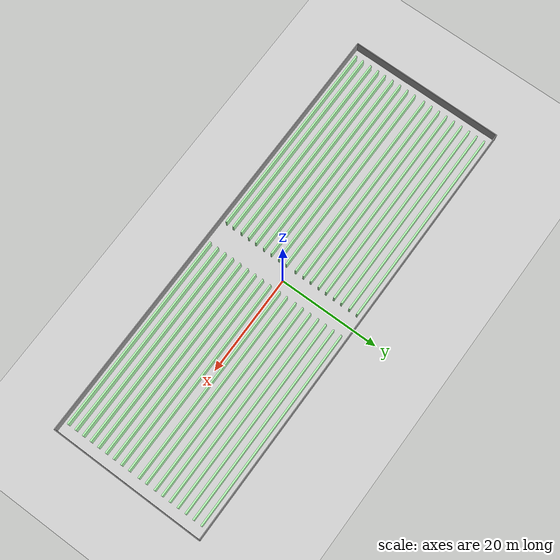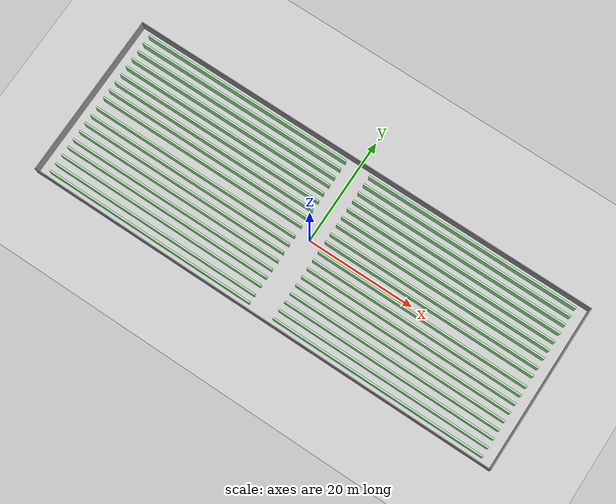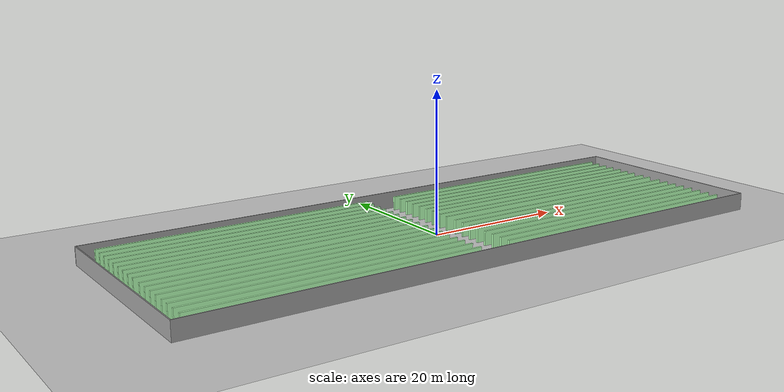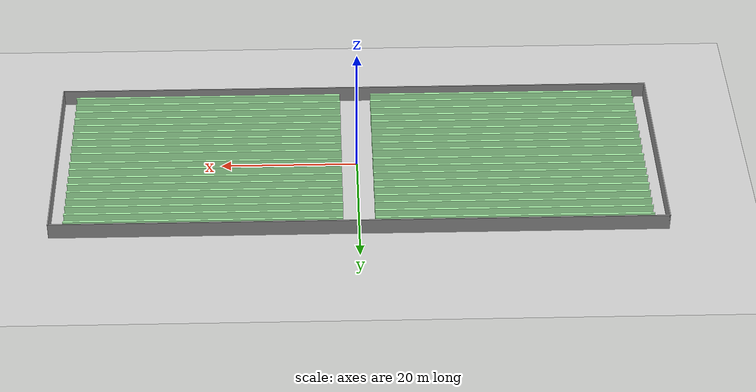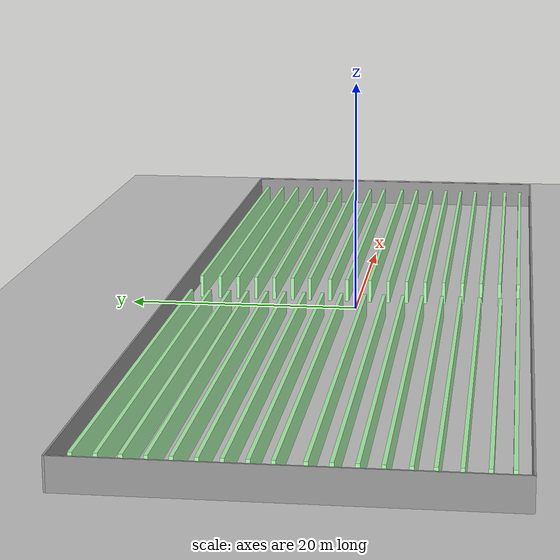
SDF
<sdf version="1.7">
 <world name="default">
  <light name="sun" type="directional">
   <pose>0 0 10 0 -0 0</pose>
   <diffuse>0.8 0.8 0.8 1</diffuse>
   <specular>0.2 0.2 0.2 1</specular>
   <attenuation>
    <range>1000</range>
    <constant>0.9</constant>
    <linear>0.01</linear>
    <quadratic>0.001</quadratic>
   </attenuation>
   <direction>-0.5 0.1 -0.9</direction>
   <spot><inner_angle>0</inner_angle><outer_angle>0</outer_angle><falloff>0</falloff></spot>
  </light>
  <model name="ground_plane">
   <static>1</static>
   <link name="link">
    <collision name="collision">
     <geometry><plane><normal>0 0 1</normal><size>100 100</size></plane></geometry>
     <surface>
      <contact><collide_bitmask>65535</collide_bitmask></contact>
      <friction><ode><mu>100</mu><mu2>50</mu2></ode></friction>
     </surface>
    </collision>
    <visual name="visual">
     <cast_shadows>0</cast_shadows>
     <geometry><plane><normal>0 0 1</normal><size>100 100</size></plane></geometry>
     <material>
      <script><uri>file://media/materials/scripts/gazebo.material</uri><name>Gazebo/Grey</name></script>
     </material>
    </visual>
   </link>
  </model>
  <gravity>0 0 -9.8</gravity>
  <magnetic_field>6e-06 2.3e-05 -4.2e-05</magnetic_field>
  <atmosphere type="adiabatic"/>
  <physics type="ode">
   <max_step_size>0.001</max_step_size>
   <real_time_factor>1</real_time_factor>
   <real_time_update_rate>1000</real_time_update_rate>
  </physics>
  <scene><ambient>0.4 0.4 0.4 1</ambient><background>0.7 0.7 0.7 1</background><shadows>1</shadows></scene>
  <spherical_coordinates>
   <surface_model>EARTH_WGS84</surface_model>
   <latitude_deg>0</latitude_deg>
   <longitude_deg>0</longitude_deg>
   <elevation>0</elevation>
   <heading_deg>0</heading_deg>
  </spherical_coordinates>
  <model name="med_inv_real">
   <link name="Wall_0">
    <collision name="Wall_0_Collision">
     <geometry><box><size>88.75 0.15 2.5</size></box></geometry>
     <pose>0 0 1.25 0 -0 0</pose>
    </collision>
    <visual name="Wall_0_Visual">
     <pose>0 0 1.25 0 -0 0</pose>
     <geometry><box><size>88.75 0.15 2.5</size></box></geometry>
     <material>
      <script><uri>file://media/materials/scripts/gazebo.material</uri><name>Gazebo/Grey</name></script>
      <ambient>1 1 1 1</ambient>
     </material>
     <meta><layer>0</layer></meta>
    </visual>
    <pose>0 15.375 0 0 -0 0</pose>
   </link>
   <link name="Wall_2">
    <collision name="Wall_2_Collision">
     <geometry><box><size>30.9 0.15 2.5</size></box></geometry>
     <pose>0 0 1.25 0 -0 0</pose>
    </collision>
    <visual name="Wall_2_Visual">
     <pose>0 0 1.25 0 -0 0</pose>
     <geometry><box><size>30.9 0.15 2.5</size></box></geometry>
     <material>
      <script><uri>file://media/materials/scripts/gazebo.material</uri><name>Gazebo/Grey</name></script>
      <ambient>1 1 1 1</ambient>
     </material>
     <meta><layer>0</layer></meta>
    </visual>
    <pose>-44.3 0 0 0 -0 -1.5708</pose>
   </link>
   <link name="Wall_3">
    <collision name="Wall_3_Collision">
     <geometry><box><size>88.75 0.15 2.5</size></box></geometry>
     <pose>0 0 1.25 0 -0 0</pose>
    </collision>
    <visual name="Wall_3_Visual">
     <pose>0 0 1.25 0 -0 0</pose>
     <geometry><box><size>88.75 0.15 2.5</size></box></geometry>
     <material>
      <script><uri>file://media/materials/scripts/gazebo.material</uri><name>Gazebo/Grey</name></script>
      <ambient>1 1 1 1</ambient>
     </material>
     <meta><layer>0</layer></meta>
    </visual>
    <pose>0 -15.375 0 0 -0 0</pose>
   </link>
   <link name="Wall_4">
    <collision name="Wall_4_Collision">
     <geometry><box><size>30.9 0.15 2.5</size></box></geometry>
     <pose>0 0 1.25 0 -0 0</pose>
    </collision>
    <visual name="Wall_4_Visual">
     <pose>0 0 1.25 0 -0 0</pose>
     <geometry><box><size>30.9 0.15 2.5</size></box></geometry>
     <material>
      <script><uri>file://media/materials/scripts/gazebo.material</uri><name>Gazebo/Grey</name></script>
      <ambient>1 1 1 1</ambient>
     </material>
     <meta><layer>0</layer></meta>
    </visual>
    <pose>44.3 0 0 0 -0 1.5708</pose>
   </link>
   <static>1</static>
  </model>
  <model name="carril_inv_real">
   <link name="link_0">
    <inertial>
     <mass>400</mass>
     <inertia><ixx>66.6667</ixx><ixy>0</ixy><ixz>0</ixz><iyy>53366.7</iyy><iyz>0</iyz><izz>53366.7</izz></inertia>
    </inertial>
    <visual name="visual">
     <geometry><box><size>40 0.3 2</size></box></geometry>
     <material>
      <lighting>1</lighting>
      <script><uri>file://media/materials/scripts/gazebo.material</uri><name>Gazebo/Grey</name></script>
      <shader type="pixel"><normal_map>__default__</normal_map></shader>
      <ambient>0.3 0.3 0.3 1</ambient>
      <diffuse>0.7 1 0.7 1</diffuse>
      <specular>0.01 1 0.01 1</specular>
      <emissive>0 1 0 1</emissive>
     </material>
    </visual>
    <collision name="collision">
     <geometry><box><size>40 0.3 2</size></box></geometry>
     <surface>
      <friction>
       <ode><mu>1</mu><mu2>1</mu2><fdir1>0 0 0</fdir1><slip1>0</slip1><slip2>0</slip2></ode>
       <torsional>
        <coefficient>1</coefficient>
        <patch_radius>0</patch_radius>
        <surface_radius>0</surface_radius>
        <use_patch_radius>1</use_patch_radius>
        <ode><slip>0</slip></ode>
       </torsional>
      </friction>
      <bounce><restitution_coefficient>0</restitution_coefficient><threshold>1e+06</threshold></bounce>
      <contact>
       <collide_without_contact>0</collide_without_contact>
       <collide_without_contact_bitmask>1</collide_without_contact_bitmask>
       <collide_bitmask>1</collide_bitmask>
       <ode>
        <soft_cfm>0</soft_cfm>
        <soft_erp>0.2</soft_erp>
        <kp>1e+13</kp>
        <kd>1</kd>
        <max_vel>0.01</max_vel>
        <min_depth>0</min_depth>
       </ode>
       <bullet>
        <split_impulse>1</split_impulse>
        <split_impulse_penetration_threshold>-0.01</split_impulse_penetration_threshold>
        <soft_cfm>0</soft_cfm>
        <soft_erp>0.2</soft_erp>
        <kp>1e+13</kp>
        <kd>1</kd>
       </bullet>
      </contact>
     </surface>
    </collision>
   </link>
   <static>0</static>
   <pose>-22.3 14.225 0.999986 0 -1e-06 -0.000337</pose>
  </model>
  <model name="carril_inv_real_clone">
   <link name="link_0">
    <inertial>
     <mass>400</mass>
     <inertia><ixx>66.6667</ixx><ixy>0</ixy><ixz>0</ixz><iyy>53366.7</iyy><iyz>0</iyz><izz>53366.7</izz></inertia>
    </inertial>
    <visual name="visual">
     <geometry><box><size>40 0.3 2</size></box></geometry>
     <material>
      <lighting>1</lighting>
      <script><uri>file://media/materials/scripts/gazebo.material</uri><name>Gazebo/Grey</name></script>
      <shader type="pixel"><normal_map>__default__</normal_map></shader>
      <ambient>0.3 0.3 0.3 1</ambient>
      <diffuse>0.7 1 0.7 1</diffuse>
      <specular>0.01 1 0.01 1</specular>
      <emissive>0 1 0 1</emissive>
     </material>
    </visual>
    <collision name="collision">
     <geometry><box><size>40 0.3 2</size></box></geometry>
     <surface>
      <friction>
       <ode><mu>1</mu><mu2>1</mu2><fdir1>0 0 0</fdir1><slip1>0</slip1><slip2>0</slip2></ode>
       <torsional>
        <coefficient>1</coefficient>
        <patch_radius>0</patch_radius>
        <surface_radius>0</surface_radius>
        <use_patch_radius>1</use_patch_radius>
        <ode><slip>0</slip></ode>
       </torsional>
      </friction>
      <bounce><restitution_coefficient>0</restitution_coefficient><threshold>1e+06</threshold></bounce>
      <contact>
       <collide_without_contact>0</collide_without_contact>
       <collide_without_contact_bitmask>1</collide_without_contact_bitmask>
       <collide_bitmask>1</collide_bitmask>
       <ode>
        <soft_cfm>0</soft_cfm>
        <soft_erp>0.2</soft_erp>
        <kp>1e+13</kp>
        <kd>1</kd>
        <max_vel>0.01</max_vel>
        <min_depth>0</min_depth>
       </ode>
       <bullet>
        <split_impulse>1</split_impulse>
        <split_impulse_penetration_threshold>-0.01</split_impulse_penetration_threshold>
        <soft_cfm>0</soft_cfm>
        <soft_erp>0.2</soft_erp>
        <kp>1e+13</kp>
        <kd>1</kd>
       </bullet>
      </contact>
     </surface>
    </collision>
   </link>
   <static>0</static>
   <pose>-22.2999 12.5908 1 0 -0 0.000855</pose>
  </model>
  <model name="carril_inv_real_clone_0">
   <link name="link_0">
    <inertial>
     <mass>400</mass>
     <inertia><ixx>66.6667</ixx><ixy>0</ixy><ixz>0</ixz><iyy>53366.7</iyy><iyz>0</iyz><izz>53366.7</izz></inertia>
    </inertial>
    <visual name="visual">
     <geometry><box><size>40 0.3 2</size></box></geometry>
     <material>
      <lighting>1</lighting>
      <script><uri>file://media/materials/scripts/gazebo.material</uri><name>Gazebo/Grey</name></script>
      <shader type="pixel"><normal_map>__default__</normal_map></shader>
      <ambient>0.3 0.3 0.3 1</ambient>
      <diffuse>0.7 1 0.7 1</diffuse>
      <specular>0.01 1 0.01 1</specular>
      <emissive>0 1 0 1</emissive>
     </material>
    </visual>
    <collision name="collision">
     <geometry><box><size>40 0.3 2</size></box></geometry>
     <surface>
      <friction>
       <ode><mu>1</mu><mu2>1</mu2><fdir1>0 0 0</fdir1><slip1>0</slip1><slip2>0</slip2></ode>
       <torsional>
        <coefficient>1</coefficient>
        <patch_radius>0</patch_radius>
        <surface_radius>0</surface_radius>
        <use_patch_radius>1</use_patch_radius>
        <ode><slip>0</slip></ode>
       </torsional>
      </friction>
      <bounce><restitution_coefficient>0</restitution_coefficient><threshold>1e+06</threshold></bounce>
      <contact>
       <collide_without_contact>0</collide_without_contact>
       <collide_without_contact_bitmask>1</collide_without_contact_bitmask>
       <collide_bitmask>1</collide_bitmask>
       <ode>
        <soft_cfm>0</soft_cfm>
        <soft_erp>0.2</soft_erp>
        <kp>1e+13</kp>
        <kd>1</kd>
        <max_vel>0.01</max_vel>
        <min_depth>0</min_depth>
       </ode>
       <bullet>
        <split_impulse>1</split_impulse>
        <split_impulse_penetration_threshold>-0.01</split_impulse_penetration_threshold>
        <soft_cfm>0</soft_cfm>
        <soft_erp>0.2</soft_erp>
        <kp>1e+13</kp>
        <kd>1</kd>
       </bullet>
      </contact>
     </surface>
    </collision>
   </link>
   <static>0</static>
   <pose>-22.2999 10.9037 0.999998 0 0 -0.000993</pose>
  </model>
  <model name="carril_inv_real_clone_1">
   <link name="link_0">
    <inertial>
     <mass>400</mass>
     <inertia><ixx>66.6667</ixx><ixy>0</ixy><ixz>0</ixz><iyy>53366.7</iyy><iyz>0</iyz><izz>53366.7</izz></inertia>
    </inertial>
    <visual name="visual">
     <geometry><box><size>40 0.3 2</size></box></geometry>
     <material>
      <lighting>1</lighting>
      <script><uri>file://media/materials/scripts/gazebo.material</uri><name>Gazebo/Grey</name></script>
      <shader type="pixel"><normal_map>__default__</normal_map></shader>
      <ambient>0.3 0.3 0.3 1</ambient>
      <diffuse>0.7 1 0.7 1</diffuse>
      <specular>0.01 1 0.01 1</specular>
      <emissive>0 1 0 1</emissive>
     </material>
    </visual>
    <collision name="collision">
     <geometry><box><size>40 0.3 2</size></box></geometry>
     <surface>
      <friction>
       <ode><mu>1</mu><mu2>1</mu2><fdir1>0 0 0</fdir1><slip1>0</slip1><slip2>0</slip2></ode>
       <torsional>
        <coefficient>1</coefficient>
        <patch_radius>0</patch_radius>
        <surface_radius>0</surface_radius>
        <use_patch_radius>1</use_patch_radius>
        <ode><slip>0</slip></ode>
       </torsional>
      </friction>
      <bounce><restitution_coefficient>0</restitution_coefficient><threshold>1e+06</threshold></bounce>
      <contact>
       <collide_without_contact>0</collide_without_contact>
       <collide_without_contact_bitmask>1</collide_without_contact_bitmask>
       <collide_bitmask>1</collide_bitmask>
       <ode>
        <soft_cfm>0</soft_cfm>
        <soft_erp>0.2</soft_erp>
        <kp>1e+13</kp>
        <kd>1</kd>
        <max_vel>0.01</max_vel>
        <min_depth>0</min_depth>
       </ode>
       <bullet>
        <split_impulse>1</split_impulse>
        <split_impulse_penetration_threshold>-0.01</split_impulse_penetration_threshold>
        <soft_cfm>0</soft_cfm>
        <soft_erp>0.2</soft_erp>
        <kp>1e+13</kp>
        <kd>1</kd>
       </bullet>
      </contact>
     </surface>
    </collision>
   </link>
   <static>0</static>
   <pose>-22.2999 9.29145 1 0 -0 0.000903</pose>
  </model>
  <model name="carril_inv_real_clone_2">
   <link name="link_0">
    <inertial>
     <mass>400</mass>
     <inertia><ixx>66.6667</ixx><ixy>0</ixy><ixz>0</ixz><iyy>53366.7</iyy><iyz>0</iyz><izz>53366.7</izz></inertia>
    </inertial>
    <visual name="visual">
     <geometry><box><size>40 0.3 2</size></box></geometry>
     <material>
      <lighting>1</lighting>
      <script><uri>file://media/materials/scripts/gazebo.material</uri><name>Gazebo/Grey</name></script>
      <shader type="pixel"><normal_map>__default__</normal_map></shader>
      <ambient>0.3 0.3 0.3 1</ambient>
      <diffuse>0.7 1 0.7 1</diffuse>
      <specular>0.01 1 0.01 1</specular>
      <emissive>0 1 0 1</emissive>
     </material>
    </visual>
    <collision name="collision">
     <geometry><box><size>40 0.3 2</size></box></geometry>
     <surface>
      <friction>
       <ode><mu>1</mu><mu2>1</mu2><fdir1>0 0 0</fdir1><slip1>0</slip1><slip2>0</slip2></ode>
       <torsional>
        <coefficient>1</coefficient>
        <patch_radius>0</patch_radius>
        <surface_radius>0</surface_radius>
        <use_patch_radius>1</use_patch_radius>
        <ode><slip>0</slip></ode>
       </torsional>
      </friction>
      <bounce><restitution_coefficient>0</restitution_coefficient><threshold>1e+06</threshold></bounce>
      <contact>
       <collide_without_contact>0</collide_without_contact>
       <collide_without_contact_bitmask>1</collide_without_contact_bitmask>
       <collide_bitmask>1</collide_bitmask>
       <ode>
        <soft_cfm>0</soft_cfm>
        <soft_erp>0.2</soft_erp>
        <kp>1e+13</kp>
        <kd>1</kd>
        <max_vel>0.01</max_vel>
        <min_depth>0</min_depth>
       </ode>
       <bullet>
        <split_impulse>1</split_impulse>
        <split_impulse_penetration_threshold>-0.01</split_impulse_penetration_threshold>
        <soft_cfm>0</soft_cfm>
        <soft_erp>0.2</soft_erp>
        <kp>1e+13</kp>
        <kd>1</kd>
       </bullet>
      </contact>
     </surface>
    </collision>
   </link>
   <static>0</static>
   <pose>-22.2999 7.60432 0.999998 0 0 -0.000945</pose>
  </model>
  <model name="carril_inv_real_clone_3">
   <link name="link_0">
    <inertial>
     <mass>400</mass>
     <inertia><ixx>66.6667</ixx><ixy>0</ixy><ixz>0</ixz><iyy>53366.7</iyy><iyz>0</iyz><izz>53366.7</izz></inertia>
    </inertial>
    <visual name="visual">
     <geometry><box><size>40 0.3 2</size></box></geometry>
     <material>
      <lighting>1</lighting>
      <script><uri>file://media/materials/scripts/gazebo.material</uri><name>Gazebo/Grey</name></script>
      <shader type="pixel"><normal_map>__default__</normal_map></shader>
      <ambient>0.3 0.3 0.3 1</ambient>
      <diffuse>0.7 1 0.7 1</diffuse>
      <specular>0.01 1 0.01 1</specular>
      <emissive>0 1 0 1</emissive>
     </material>
    </visual>
    <collision name="collision">
     <geometry><box><size>40 0.3 2</size></box></geometry>
     <surface>
      <friction>
       <ode><mu>1</mu><mu2>1</mu2><fdir1>0 0 0</fdir1><slip1>0</slip1><slip2>0</slip2></ode>
       <torsional>
        <coefficient>1</coefficient>
        <patch_radius>0</patch_radius>
        <surface_radius>0</surface_radius>
        <use_patch_radius>1</use_patch_radius>
        <ode><slip>0</slip></ode>
       </torsional>
      </friction>
      <bounce><restitution_coefficient>0</restitution_coefficient><threshold>1e+06</threshold></bounce>
      <contact>
       <collide_without_contact>0</collide_without_contact>
       <collide_without_contact_bitmask>1</collide_without_contact_bitmask>
       <collide_bitmask>1</collide_bitmask>
       <ode>
        <soft_cfm>0</soft_cfm>
        <soft_erp>0.2</soft_erp>
        <kp>1e+13</kp>
        <kd>1</kd>
        <max_vel>0.01</max_vel>
        <min_depth>0</min_depth>
       </ode>
       <bullet>
        <split_impulse>1</split_impulse>
        <split_impulse_penetration_threshold>-0.01</split_impulse_penetration_threshold>
        <soft_cfm>0</soft_cfm>
        <soft_erp>0.2</soft_erp>
        <kp>1e+13</kp>
        <kd>1</kd>
       </bullet>
      </contact>
     </surface>
    </collision>
   </link>
   <static>0</static>
   <pose>-22.2999 5.9921 1 0 -0 0.000952</pose>
  </model>
  <model name="carril_inv_real_clone_4">
   <link name="link_0">
    <inertial>
     <mass>400</mass>
     <inertia><ixx>66.6667</ixx><ixy>0</ixy><ixz>0</ixz><iyy>53366.7</iyy><iyz>0</iyz><izz>53366.7</izz></inertia>
    </inertial>
    <visual name="visual">
     <geometry><box><size>40 0.3 2</size></box></geometry>
     <material>
      <lighting>1</lighting>
      <script><uri>file://media/materials/scripts/gazebo.material</uri><name>Gazebo/Grey</name></script>
      <shader type="pixel"><normal_map>__default__</normal_map></shader>
      <ambient>0.3 0.3 0.3 1</ambient>
      <diffuse>0.7 1 0.7 1</diffuse>
      <specular>0.01 1 0.01 1</specular>
      <emissive>0 1 0 1</emissive>
     </material>
    </visual>
    <collision name="collision">
     <geometry><box><size>40 0.3 2</size></box></geometry>
     <surface>
      <friction>
       <ode><mu>1</mu><mu2>1</mu2><fdir1>0 0 0</fdir1><slip1>0</slip1><slip2>0</slip2></ode>
       <torsional>
        <coefficient>1</coefficient>
        <patch_radius>0</patch_radius>
        <surface_radius>0</surface_radius>
        <use_patch_radius>1</use_patch_radius>
        <ode><slip>0</slip></ode>
       </torsional>
      </friction>
      <bounce><restitution_coefficient>0</restitution_coefficient><threshold>1e+06</threshold></bounce>
      <contact>
       <collide_without_contact>0</collide_without_contact>
       <collide_without_contact_bitmask>1</collide_without_contact_bitmask>
       <collide_bitmask>1</collide_bitmask>
       <ode>
        <soft_cfm>0</soft_cfm>
        <soft_erp>0.2</soft_erp>
        <kp>1e+13</kp>
        <kd>1</kd>
        <max_vel>0.01</max_vel>
        <min_depth>0</min_depth>
       </ode>
       <bullet>
        <split_impulse>1</split_impulse>
        <split_impulse_penetration_threshold>-0.01</split_impulse_penetration_threshold>
        <soft_cfm>0</soft_cfm>
        <soft_erp>0.2</soft_erp>
        <kp>1e+13</kp>
        <kd>1</kd>
       </bullet>
      </contact>
     </surface>
    </collision>
   </link>
   <static>0</static>
   <pose>-22.2999 4.30497 0.999998 0 0 -0.000896</pose>
  </model>
  <model name="carril_inv_real_clone_6">
   <link name="link_0">
    <inertial>
     <mass>400</mass>
     <inertia><ixx>66.6667</ixx><ixy>0</ixy><ixz>0</ixz><iyy>53366.7</iyy><iyz>0</iyz><izz>53366.7</izz></inertia>
    </inertial>
    <visual name="visual">
     <geometry><box><size>40 0.3 2</size></box></geometry>
     <material>
      <lighting>1</lighting>
      <script><uri>file://media/materials/scripts/gazebo.material</uri><name>Gazebo/Grey</name></script>
      <shader type="pixel"><normal_map>__default__</normal_map></shader>
      <ambient>0.3 0.3 0.3 1</ambient>
      <diffuse>0.7 1 0.7 1</diffuse>
      <specular>0.01 1 0.01 1</specular>
      <emissive>0 1 0 1</emissive>
     </material>
    </visual>
    <collision name="collision">
     <geometry><box><size>40 0.3 2</size></box></geometry>
     <surface>
      <friction>
       <ode><mu>1</mu><mu2>1</mu2><fdir1>0 0 0</fdir1><slip1>0</slip1><slip2>0</slip2></ode>
       <torsional>
        <coefficient>1</coefficient>
        <patch_radius>0</patch_radius>
        <surface_radius>0</surface_radius>
        <use_patch_radius>1</use_patch_radius>
        <ode><slip>0</slip></ode>
       </torsional>
      </friction>
      <bounce><restitution_coefficient>0</restitution_coefficient><threshold>1e+06</threshold></bounce>
      <contact>
       <collide_without_contact>0</collide_without_contact>
       <collide_without_contact_bitmask>1</collide_without_contact_bitmask>
       <collide_bitmask>1</collide_bitmask>
       <ode>
        <soft_cfm>0</soft_cfm>
        <soft_erp>0.2</soft_erp>
        <kp>1e+13</kp>
        <kd>1</kd>
        <max_vel>0.01</max_vel>
        <min_depth>0</min_depth>
       </ode>
       <bullet>
        <split_impulse>1</split_impulse>
        <split_impulse_penetration_threshold>-0.01</split_impulse_penetration_threshold>
        <soft_cfm>0</soft_cfm>
        <soft_erp>0.2</soft_erp>
        <kp>1e+13</kp>
        <kd>1</kd>
       </bullet>
      </contact>
     </surface>
    </collision>
   </link>
   <static>0</static>
   <pose>-22.3 2.675 0.999986 0 -1e-06 0.000227</pose>
  </model>
  <model name="carril_inv_real_clone_7">
   <link name="link_0">
    <inertial>
     <mass>400</mass>
     <inertia><ixx>66.6667</ixx><ixy>0</ixy><ixz>0</ixz><iyy>53366.7</iyy><iyz>0</iyz><izz>53366.7</izz></inertia>
    </inertial>
    <visual name="visual">
     <geometry><box><size>40 0.3 2</size></box></geometry>
     <material>
      <lighting>1</lighting>
      <script><uri>file://media/materials/scripts/gazebo.material</uri><name>Gazebo/Grey</name></script>
      <shader type="pixel"><normal_map>__default__</normal_map></shader>
      <ambient>0.3 0.3 0.3 1</ambient>
      <diffuse>0.7 1 0.7 1</diffuse>
      <specular>0.01 1 0.01 1</specular>
      <emissive>0 1 0 1</emissive>
     </material>
    </visual>
    <collision name="collision">
     <geometry><box><size>40 0.3 2</size></box></geometry>
     <surface>
      <friction>
       <ode><mu>1</mu><mu2>1</mu2><fdir1>0 0 0</fdir1><slip1>0</slip1><slip2>0</slip2></ode>
       <torsional>
        <coefficient>1</coefficient>
        <patch_radius>0</patch_radius>
        <surface_radius>0</surface_radius>
        <use_patch_radius>1</use_patch_radius>
        <ode><slip>0</slip></ode>
       </torsional>
      </friction>
      <bounce><restitution_coefficient>0</restitution_coefficient><threshold>1e+06</threshold></bounce>
      <contact>
       <collide_without_contact>0</collide_without_contact>
       <collide_without_contact_bitmask>1</collide_without_contact_bitmask>
       <collide_bitmask>1</collide_bitmask>
       <ode>
        <soft_cfm>0</soft_cfm>
        <soft_erp>0.2</soft_erp>
        <kp>1e+13</kp>
        <kd>1</kd>
        <max_vel>0.01</max_vel>
        <min_depth>0</min_depth>
       </ode>
       <bullet>
        <split_impulse>1</split_impulse>
        <split_impulse_penetration_threshold>-0.01</split_impulse_penetration_threshold>
        <soft_cfm>0</soft_cfm>
        <soft_erp>0.2</soft_erp>
        <kp>1e+13</kp>
        <kd>1</kd>
       </bullet>
      </contact>
     </surface>
    </collision>
   </link>
   <static>0</static>
   <pose>-22.3 1.025 0.999986 0 -1e-06 -0.000316</pose>
  </model>
  <model name="carril_inv_real_clone_7_clone">
   <link name="link_0">
    <inertial>
     <mass>400</mass>
     <inertia><ixx>66.6667</ixx><ixy>0</ixy><ixz>0</ixz><iyy>53366.7</iyy><iyz>0</iyz><izz>53366.7</izz></inertia>
    </inertial>
    <visual name="visual">
     <geometry><box><size>40 0.3 2</size></box></geometry>
     <material>
      <lighting>1</lighting>
      <script><uri>file://media/materials/scripts/gazebo.material</uri><name>Gazebo/Grey</name></script>
      <shader type="pixel"><normal_map>__default__</normal_map></shader>
      <ambient>0.3 0.3 0.3 1</ambient>
      <diffuse>0.7 1 0.7 1</diffuse>
      <specular>0.01 1 0.01 1</specular>
      <emissive>0 1 0 1</emissive>
     </material>
    </visual>
    <collision name="collision">
     <geometry><box><size>40 0.3 2</size></box></geometry>
     <surface>
      <friction>
       <ode><mu>1</mu><mu2>1</mu2><fdir1>0 0 0</fdir1><slip1>0</slip1><slip2>0</slip2></ode>
       <torsional>
        <coefficient>1</coefficient>
        <patch_radius>0</patch_radius>
        <surface_radius>0</surface_radius>
        <use_patch_radius>1</use_patch_radius>
        <ode><slip>0</slip></ode>
       </torsional>
      </friction>
      <bounce><restitution_coefficient>0</restitution_coefficient><threshold>1e+06</threshold></bounce>
      <contact>
       <collide_without_contact>0</collide_without_contact>
       <collide_without_contact_bitmask>1</collide_without_contact_bitmask>
       <collide_bitmask>1</collide_bitmask>
       <ode>
        <soft_cfm>0</soft_cfm>
        <soft_erp>0.2</soft_erp>
        <kp>1e+13</kp>
        <kd>1</kd>
        <max_vel>0.01</max_vel>
        <min_depth>0</min_depth>
       </ode>
       <bullet>
        <split_impulse>1</split_impulse>
        <split_impulse_penetration_threshold>-0.01</split_impulse_penetration_threshold>
        <soft_cfm>0</soft_cfm>
        <soft_erp>0.2</soft_erp>
        <kp>1e+13</kp>
        <kd>1</kd>
       </bullet>
      </contact>
     </surface>
    </collision>
   </link>
   <static>0</static>
   <pose>-22.3 -1.025 0.999986 0 1e-06 -0.000235</pose>
  </model>
  <model name="carril_inv_real_clone_7_clone_0">
   <link name="link_0">
    <inertial>
     <mass>400</mass>
     <inertia><ixx>66.6667</ixx><ixy>0</ixy><ixz>0</ixz><iyy>53366.7</iyy><iyz>0</iyz><izz>53366.7</izz></inertia>
    </inertial>
    <visual name="visual">
     <geometry><box><size>40 0.3 2</size></box></geometry>
     <material>
      <lighting>1</lighting>
      <script><uri>file://media/materials/scripts/gazebo.material</uri><name>Gazebo/Grey</name></script>
      <shader type="pixel"><normal_map>__default__</normal_map></shader>
      <ambient>0.3 0.3 0.3 1</ambient>
      <diffuse>0.7 1 0.7 1</diffuse>
      <specular>0.01 1 0.01 1</specular>
      <emissive>0 1 0 1</emissive>
     </material>
    </visual>
    <collision name="collision">
     <geometry><box><size>40 0.3 2</size></box></geometry>
     <surface>
      <friction>
       <ode><mu>1</mu><mu2>1</mu2><fdir1>0 0 0</fdir1><slip1>0</slip1><slip2>0</slip2></ode>
       <torsional>
        <coefficient>1</coefficient>
        <patch_radius>0</patch_radius>
        <surface_radius>0</surface_radius>
        <use_patch_radius>1</use_patch_radius>
        <ode><slip>0</slip></ode>
       </torsional>
      </friction>
      <bounce><restitution_coefficient>0</restitution_coefficient><threshold>1e+06</threshold></bounce>
      <contact>
       <collide_without_contact>0</collide_without_contact>
       <collide_without_contact_bitmask>1</collide_without_contact_bitmask>
       <collide_bitmask>1</collide_bitmask>
       <ode>
        <soft_cfm>0</soft_cfm>
        <soft_erp>0.2</soft_erp>
        <kp>1e+13</kp>
        <kd>1</kd>
        <max_vel>0.01</max_vel>
        <min_depth>0</min_depth>
       </ode>
       <bullet>
        <split_impulse>1</split_impulse>
        <split_impulse_penetration_threshold>-0.01</split_impulse_penetration_threshold>
        <soft_cfm>0</soft_cfm>
        <soft_erp>0.2</soft_erp>
        <kp>1e+13</kp>
        <kd>1</kd>
       </bullet>
      </contact>
     </surface>
    </collision>
   </link>
   <static>0</static>
   <pose>-22.3 -2.675 0.999986 0 -1e-06 -0.00024</pose>
  </model>
  <model name="carril_inv_real_clone_7_clone_1">
   <link name="link_0">
    <inertial>
     <mass>400</mass>
     <inertia><ixx>66.6667</ixx><ixy>0</ixy><ixz>0</ixz><iyy>53366.7</iyy><iyz>0</iyz><izz>53366.7</izz></inertia>
    </inertial>
    <visual name="visual">
     <geometry><box><size>40 0.3 2</size></box></geometry>
     <material>
      <lighting>1</lighting>
      <script><uri>file://media/materials/scripts/gazebo.material</uri><name>Gazebo/Grey</name></script>
      <shader type="pixel"><normal_map>__default__</normal_map></shader>
      <ambient>0.3 0.3 0.3 1</ambient>
      <diffuse>0.7 1 0.7 1</diffuse>
      <specular>0.01 1 0.01 1</specular>
      <emissive>0 1 0 1</emissive>
     </material>
    </visual>
    <collision name="collision">
     <geometry><box><size>40 0.3 2</size></box></geometry>
     <surface>
      <friction>
       <ode><mu>1</mu><mu2>1</mu2><fdir1>0 0 0</fdir1><slip1>0</slip1><slip2>0</slip2></ode>
       <torsional>
        <coefficient>1</coefficient>
        <patch_radius>0</patch_radius>
        <surface_radius>0</surface_radius>
        <use_patch_radius>1</use_patch_radius>
        <ode><slip>0</slip></ode>
       </torsional>
      </friction>
      <bounce><restitution_coefficient>0</restitution_coefficient><threshold>1e+06</threshold></bounce>
      <contact>
       <collide_without_contact>0</collide_without_contact>
       <collide_without_contact_bitmask>1</collide_without_contact_bitmask>
       <collide_bitmask>1</collide_bitmask>
       <ode>
        <soft_cfm>0</soft_cfm>
        <soft_erp>0.2</soft_erp>
        <kp>1e+13</kp>
        <kd>1</kd>
        <max_vel>0.01</max_vel>
        <min_depth>0</min_depth>
       </ode>
       <bullet>
        <split_impulse>1</split_impulse>
        <split_impulse_penetration_threshold>-0.01</split_impulse_penetration_threshold>
        <soft_cfm>0</soft_cfm>
        <soft_erp>0.2</soft_erp>
        <kp>1e+13</kp>
        <kd>1</kd>
       </bullet>
      </contact>
     </surface>
    </collision>
   </link>
   <static>0</static>
   <pose>-22.3 -4.325 0.999986 -0 1e-06 0.000109</pose>
  </model>
  <model name="carril_inv_real_clone_7_clone_2">
   <link name="link_0">
    <inertial>
     <mass>400</mass>
     <inertia><ixx>66.6667</ixx><ixy>0</ixy><ixz>0</ixz><iyy>53366.7</iyy><iyz>0</iyz><izz>53366.7</izz></inertia>
    </inertial>
    <visual name="visual">
     <geometry><box><size>40 0.3 2</size></box></geometry>
     <material>
      <lighting>1</lighting>
      <script><uri>file://media/materials/scripts/gazebo.material</uri><name>Gazebo/Grey</name></script>
      <shader type="pixel"><normal_map>__default__</normal_map></shader>
      <ambient>0.3 0.3 0.3 1</ambient>
      <diffuse>0.7 1 0.7 1</diffuse>
      <specular>0.01 1 0.01 1</specular>
      <emissive>0 1 0 1</emissive>
     </material>
    </visual>
    <collision name="collision">
     <geometry><box><size>40 0.3 2</size></box></geometry>
     <surface>
      <friction>
       <ode><mu>1</mu><mu2>1</mu2><fdir1>0 0 0</fdir1><slip1>0</slip1><slip2>0</slip2></ode>
       <torsional>
        <coefficient>1</coefficient>
        <patch_radius>0</patch_radius>
        <surface_radius>0</surface_radius>
        <use_patch_radius>1</use_patch_radius>
        <ode><slip>0</slip></ode>
       </torsional>
      </friction>
      <bounce><restitution_coefficient>0</restitution_coefficient><threshold>1e+06</threshold></bounce>
      <contact>
       <collide_without_contact>0</collide_without_contact>
       <collide_without_contact_bitmask>1</collide_without_contact_bitmask>
       <collide_bitmask>1</collide_bitmask>
       <ode>
        <soft_cfm>0</soft_cfm>
        <soft_erp>0.2</soft_erp>
        <kp>1e+13</kp>
        <kd>1</kd>
        <max_vel>0.01</max_vel>
        <min_depth>0</min_depth>
       </ode>
       <bullet>
        <split_impulse>1</split_impulse>
        <split_impulse_penetration_threshold>-0.01</split_impulse_penetration_threshold>
        <soft_cfm>0</soft_cfm>
        <soft_erp>0.2</soft_erp>
        <kp>1e+13</kp>
        <kd>1</kd>
       </bullet>
      </contact>
     </surface>
    </collision>
   </link>
   <static>0</static>
   <pose>-22.3 -5.975 0.999986 0 -1e-06 0.000103</pose>
  </model>
  <model name="carril_inv_real_clone_7_clone_3">
   <link name="link_0">
    <inertial>
     <mass>400</mass>
     <inertia><ixx>66.6667</ixx><ixy>0</ixy><ixz>0</ixz><iyy>53366.7</iyy><iyz>0</iyz><izz>53366.7</izz></inertia>
    </inertial>
    <visual name="visual">
     <geometry><box><size>40 0.3 2</size></box></geometry>
     <material>
      <lighting>1</lighting>
      <script><uri>file://media/materials/scripts/gazebo.material</uri><name>Gazebo/Grey</name></script>
      <shader type="pixel"><normal_map>__default__</normal_map></shader>
      <ambient>0.3 0.3 0.3 1</ambient>
      <diffuse>0.7 1 0.7 1</diffuse>
      <specular>0.01 1 0.01 1</specular>
      <emissive>0 1 0 1</emissive>
     </material>
    </visual>
    <collision name="collision">
     <geometry><box><size>40 0.3 2</size></box></geometry>
     <surface>
      <friction>
       <ode><mu>1</mu><mu2>1</mu2><fdir1>0 0 0</fdir1><slip1>0</slip1><slip2>0</slip2></ode>
       <torsional>
        <coefficient>1</coefficient>
        <patch_radius>0</patch_radius>
        <surface_radius>0</surface_radius>
        <use_patch_radius>1</use_patch_radius>
        <ode><slip>0</slip></ode>
       </torsional>
      </friction>
      <bounce><restitution_coefficient>0</restitution_coefficient><threshold>1e+06</threshold></bounce>
      <contact>
       <collide_without_contact>0</collide_without_contact>
       <collide_without_contact_bitmask>1</collide_without_contact_bitmask>
       <collide_bitmask>1</collide_bitmask>
       <ode>
        <soft_cfm>0</soft_cfm>
        <soft_erp>0.2</soft_erp>
        <kp>1e+13</kp>
        <kd>1</kd>
        <max_vel>0.01</max_vel>
        <min_depth>0</min_depth>
       </ode>
       <bullet>
        <split_impulse>1</split_impulse>
        <split_impulse_penetration_threshold>-0.01</split_impulse_penetration_threshold>
        <soft_cfm>0</soft_cfm>
        <soft_erp>0.2</soft_erp>
        <kp>1e+13</kp>
        <kd>1</kd>
       </bullet>
      </contact>
     </surface>
    </collision>
   </link>
   <static>0</static>
   <pose>-22.2999 -7.70917 1 0 -0 0.00043</pose>
  </model>
  <model name="carril_inv_real_clone_7_clone_4">
   <link name="link_0">
    <inertial>
     <mass>400</mass>
     <inertia><ixx>66.6667</ixx><ixy>0</ixy><ixz>0</ixz><iyy>53366.7</iyy><iyz>0</iyz><izz>53366.7</izz></inertia>
    </inertial>
    <visual name="visual">
     <geometry><box><size>40 0.3 2</size></box></geometry>
     <material>
      <lighting>1</lighting>
      <script><uri>file://media/materials/scripts/gazebo.material</uri><name>Gazebo/Grey</name></script>
      <shader type="pixel"><normal_map>__default__</normal_map></shader>
      <ambient>0.3 0.3 0.3 1</ambient>
      <diffuse>0.7 1 0.7 1</diffuse>
      <specular>0.01 1 0.01 1</specular>
      <emissive>0 1 0 1</emissive>
     </material>
    </visual>
    <collision name="collision">
     <geometry><box><size>40 0.3 2</size></box></geometry>
     <surface>
      <friction>
       <ode><mu>1</mu><mu2>1</mu2><fdir1>0 0 0</fdir1><slip1>0</slip1><slip2>0</slip2></ode>
       <torsional>
        <coefficient>1</coefficient>
        <patch_radius>0</patch_radius>
        <surface_radius>0</surface_radius>
        <use_patch_radius>1</use_patch_radius>
        <ode><slip>0</slip></ode>
       </torsional>
      </friction>
      <bounce><restitution_coefficient>0</restitution_coefficient><threshold>1e+06</threshold></bounce>
      <contact>
       <collide_without_contact>0</collide_without_contact>
       <collide_without_contact_bitmask>1</collide_without_contact_bitmask>
       <collide_bitmask>1</collide_bitmask>
       <ode>
        <soft_cfm>0</soft_cfm>
        <soft_erp>0.2</soft_erp>
        <kp>1e+13</kp>
        <kd>1</kd>
        <max_vel>0.01</max_vel>
        <min_depth>0</min_depth>
       </ode>
       <bullet>
        <split_impulse>1</split_impulse>
        <split_impulse_penetration_threshold>-0.01</split_impulse_penetration_threshold>
        <soft_cfm>0</soft_cfm>
        <soft_erp>0.2</soft_erp>
        <kp>1e+13</kp>
        <kd>1</kd>
       </bullet>
      </contact>
     </surface>
    </collision>
   </link>
   <static>0</static>
   <pose>-22.3001 -9.27229 1 0 0 -0.000737</pose>
  </model>
  <model name="carril_inv_real_clone_7_clone_5">
   <link name="link_0">
    <inertial>
     <mass>400</mass>
     <inertia><ixx>66.6667</ixx><ixy>0</ixy><ixz>0</ixz><iyy>53366.7</iyy><iyz>0</iyz><izz>53366.7</izz></inertia>
    </inertial>
    <visual name="visual">
     <geometry><box><size>40 0.3 2</size></box></geometry>
     <material>
      <lighting>1</lighting>
      <script><uri>file://media/materials/scripts/gazebo.material</uri><name>Gazebo/Grey</name></script>
      <shader type="pixel"><normal_map>__default__</normal_map></shader>
      <ambient>0.3 0.3 0.3 1</ambient>
      <diffuse>0.7 1 0.7 1</diffuse>
      <specular>0.01 1 0.01 1</specular>
      <emissive>0 1 0 1</emissive>
     </material>
    </visual>
    <collision name="collision">
     <geometry><box><size>40 0.3 2</size></box></geometry>
     <surface>
      <friction>
       <ode><mu>1</mu><mu2>1</mu2><fdir1>0 0 0</fdir1><slip1>0</slip1><slip2>0</slip2></ode>
       <torsional>
        <coefficient>1</coefficient>
        <patch_radius>0</patch_radius>
        <surface_radius>0</surface_radius>
        <use_patch_radius>1</use_patch_radius>
        <ode><slip>0</slip></ode>
       </torsional>
      </friction>
      <bounce><restitution_coefficient>0</restitution_coefficient><threshold>1e+06</threshold></bounce>
      <contact>
       <collide_without_contact>0</collide_without_contact>
       <collide_without_contact_bitmask>1</collide_without_contact_bitmask>
       <collide_bitmask>1</collide_bitmask>
       <ode>
        <soft_cfm>0</soft_cfm>
        <soft_erp>0.2</soft_erp>
        <kp>1e+13</kp>
        <kd>1</kd>
        <max_vel>0.01</max_vel>
        <min_depth>0</min_depth>
       </ode>
       <bullet>
        <split_impulse>1</split_impulse>
        <split_impulse_penetration_threshold>-0.01</split_impulse_penetration_threshold>
        <soft_cfm>0</soft_cfm>
        <soft_erp>0.2</soft_erp>
        <kp>1e+13</kp>
        <kd>1</kd>
       </bullet>
      </contact>
     </surface>
    </collision>
   </link>
   <static>0</static>
   <pose>-22.3 -10.9237 0.999986 0 1e-06 -0.000274</pose>
  </model>
  <model name="carril_inv_real_clone_7_clone_6">
   <link name="link_0">
    <inertial>
     <mass>400</mass>
     <inertia><ixx>66.6667</ixx><ixy>0</ixy><ixz>0</ixz><iyy>53366.7</iyy><iyz>0</iyz><izz>53366.7</izz></inertia>
    </inertial>
    <visual name="visual">
     <geometry><box><size>40 0.3 2</size></box></geometry>
     <material>
      <lighting>1</lighting>
      <script><uri>file://media/materials/scripts/gazebo.material</uri><name>Gazebo/Grey</name></script>
      <shader type="pixel"><normal_map>__default__</normal_map></shader>
      <ambient>0.3 0.3 0.3 1</ambient>
      <diffuse>0.7 1 0.7 1</diffuse>
      <specular>0.01 1 0.01 1</specular>
      <emissive>0 1 0 1</emissive>
     </material>
    </visual>
    <collision name="collision">
     <geometry><box><size>40 0.3 2</size></box></geometry>
     <surface>
      <friction>
       <ode><mu>1</mu><mu2>1</mu2><fdir1>0 0 0</fdir1><slip1>0</slip1><slip2>0</slip2></ode>
       <torsional>
        <coefficient>1</coefficient>
        <patch_radius>0</patch_radius>
        <surface_radius>0</surface_radius>
        <use_patch_radius>1</use_patch_radius>
        <ode><slip>0</slip></ode>
       </torsional>
      </friction>
      <bounce><restitution_coefficient>0</restitution_coefficient><threshold>1e+06</threshold></bounce>
      <contact>
       <collide_without_contact>0</collide_without_contact>
       <collide_without_contact_bitmask>1</collide_without_contact_bitmask>
       <collide_bitmask>1</collide_bitmask>
       <ode>
        <soft_cfm>0</soft_cfm>
        <soft_erp>0.2</soft_erp>
        <kp>1e+13</kp>
        <kd>1</kd>
        <max_vel>0.01</max_vel>
        <min_depth>0</min_depth>
       </ode>
       <bullet>
        <split_impulse>1</split_impulse>
        <split_impulse_penetration_threshold>-0.01</split_impulse_penetration_threshold>
        <soft_cfm>0</soft_cfm>
        <soft_erp>0.2</soft_erp>
        <kp>1e+13</kp>
        <kd>1</kd>
       </bullet>
      </contact>
     </surface>
    </collision>
   </link>
   <static>0</static>
   <pose>-22.3001 -12.6987 1 0 0 -0.000688</pose>
  </model>
  <model name="carril_inv_real_clone_7_clone_7">
   <link name="link_0">
    <inertial>
     <mass>400</mass>
     <inertia><ixx>66.6667</ixx><ixy>0</ixy><ixz>0</ixz><iyy>53366.7</iyy><iyz>0</iyz><izz>53366.7</izz></inertia>
    </inertial>
    <visual name="visual">
     <geometry><box><size>40 0.3 2</size></box></geometry>
     <material>
      <lighting>1</lighting>
      <script><uri>file://media/materials/scripts/gazebo.material</uri><name>Gazebo/Grey</name></script>
      <shader type="pixel"><normal_map>__default__</normal_map></shader>
      <ambient>0.3 0.3 0.3 1</ambient>
      <diffuse>0.7 1 0.7 1</diffuse>
      <specular>0.01 1 0.01 1</specular>
      <emissive>0 1 0 1</emissive>
     </material>
    </visual>
    <collision name="collision">
     <geometry><box><size>40 0.3 2</size></box></geometry>
     <surface>
      <friction>
       <ode><mu>1</mu><mu2>1</mu2><fdir1>0 0 0</fdir1><slip1>0</slip1><slip2>0</slip2></ode>
       <torsional>
        <coefficient>1</coefficient>
        <patch_radius>0</patch_radius>
        <surface_radius>0</surface_radius>
        <use_patch_radius>1</use_patch_radius>
        <ode><slip>0</slip></ode>
       </torsional>
      </friction>
      <bounce><restitution_coefficient>0</restitution_coefficient><threshold>1e+06</threshold></bounce>
      <contact>
       <collide_without_contact>0</collide_without_contact>
       <collide_without_contact_bitmask>1</collide_without_contact_bitmask>
       <collide_bitmask>1</collide_bitmask>
       <ode>
        <soft_cfm>0</soft_cfm>
        <soft_erp>0.2</soft_erp>
        <kp>1e+13</kp>
        <kd>1</kd>
        <max_vel>0.01</max_vel>
        <min_depth>0</min_depth>
       </ode>
       <bullet>
        <split_impulse>1</split_impulse>
        <split_impulse_penetration_threshold>-0.01</split_impulse_penetration_threshold>
        <soft_cfm>0</soft_cfm>
        <soft_erp>0.2</soft_erp>
        <kp>1e+13</kp>
        <kd>1</kd>
       </bullet>
      </contact>
     </surface>
    </collision>
   </link>
   <static>0</static>
   <pose>-22.3 -14.225 0.999986 -0 -1e-06 -0.000283</pose>
  </model>
  <model name="carril_inv_real_clone_5">
   <link name="link_0">
    <inertial>
     <mass>400</mass>
     <inertia><ixx>66.6667</ixx><ixy>0</ixy><ixz>0</ixz><iyy>53366.7</iyy><iyz>0</iyz><izz>53366.7</izz></inertia>
    </inertial>
    <visual name="visual">
     <geometry><box><size>40 0.3 2</size></box></geometry>
     <material>
      <lighting>1</lighting>
      <script><uri>file://media/materials/scripts/gazebo.material</uri><name>Gazebo/Grey</name></script>
      <shader type="pixel"><normal_map>__default__</normal_map></shader>
      <ambient>0.3 0.3 0.3 1</ambient>
      <diffuse>0.7 1 0.7 1</diffuse>
      <specular>0.01 1 0.01 1</specular>
      <emissive>0 1 0 1</emissive>
     </material>
    </visual>
    <collision name="collision">
     <geometry><box><size>40 0.3 2</size></box></geometry>
     <surface>
      <friction>
       <ode><mu>1</mu><mu2>1</mu2><fdir1>0 0 0</fdir1><slip1>0</slip1><slip2>0</slip2></ode>
       <torsional>
        <coefficient>1</coefficient>
        <patch_radius>0</patch_radius>
        <surface_radius>0</surface_radius>
        <use_patch_radius>1</use_patch_radius>
        <ode><slip>0</slip></ode>
       </torsional>
      </friction>
      <bounce><restitution_coefficient>0</restitution_coefficient><threshold>1e+06</threshold></bounce>
      <contact>
       <collide_without_contact>0</collide_without_contact>
       <collide_without_contact_bitmask>1</collide_without_contact_bitmask>
       <collide_bitmask>1</collide_bitmask>
       <ode>
        <soft_cfm>0</soft_cfm>
        <soft_erp>0.2</soft_erp>
        <kp>1e+13</kp>
        <kd>1</kd>
        <max_vel>0.01</max_vel>
        <min_depth>0</min_depth>
       </ode>
       <bullet>
        <split_impulse>1</split_impulse>
        <split_impulse_penetration_threshold>-0.01</split_impulse_penetration_threshold>
        <soft_cfm>0</soft_cfm>
        <soft_erp>0.2</soft_erp>
        <kp>1e+13</kp>
        <kd>1</kd>
       </bullet>
      </contact>
     </surface>
    </collision>
   </link>
   <static>0</static>
   <pose>22.3 14.225 0.999986 0 -1e-06 -6.1e-05</pose>
  </model>
  <model name="carril_inv_real_clone_8">
   <link name="link_0">
    <inertial>
     <mass>400</mass>
     <inertia><ixx>66.6667</ixx><ixy>0</ixy><ixz>0</ixz><iyy>53366.7</iyy><iyz>0</iyz><izz>53366.7</izz></inertia>
    </inertial>
    <visual name="visual">
     <geometry><box><size>40 0.3 2</size></box></geometry>
     <material>
      <lighting>1</lighting>
      <script><uri>file://media/materials/scripts/gazebo.material</uri><name>Gazebo/Grey</name></script>
      <shader type="pixel"><normal_map>__default__</normal_map></shader>
      <ambient>0.3 0.3 0.3 1</ambient>
      <diffuse>0.7 1 0.7 1</diffuse>
      <specular>0.01 1 0.01 1</specular>
      <emissive>0 1 0 1</emissive>
     </material>
    </visual>
    <collision name="collision">
     <geometry><box><size>40 0.3 2</size></box></geometry>
     <surface>
      <friction>
       <ode><mu>1</mu><mu2>1</mu2><fdir1>0 0 0</fdir1><slip1>0</slip1><slip2>0</slip2></ode>
       <torsional>
        <coefficient>1</coefficient>
        <patch_radius>0</patch_radius>
        <surface_radius>0</surface_radius>
        <use_patch_radius>1</use_patch_radius>
        <ode><slip>0</slip></ode>
       </torsional>
      </friction>
      <bounce><restitution_coefficient>0</restitution_coefficient><threshold>1e+06</threshold></bounce>
      <contact>
       <collide_without_contact>0</collide_without_contact>
       <collide_without_contact_bitmask>1</collide_without_contact_bitmask>
       <collide_bitmask>1</collide_bitmask>
       <ode>
        <soft_cfm>0</soft_cfm>
        <soft_erp>0.2</soft_erp>
        <kp>1e+13</kp>
        <kd>1</kd>
        <max_vel>0.01</max_vel>
        <min_depth>0</min_depth>
       </ode>
       <bullet>
        <split_impulse>1</split_impulse>
        <split_impulse_penetration_threshold>-0.01</split_impulse_penetration_threshold>
        <soft_cfm>0</soft_cfm>
        <soft_erp>0.2</soft_erp>
        <kp>1e+13</kp>
        <kd>1</kd>
       </bullet>
      </contact>
     </surface>
    </collision>
   </link>
   <static>0</static>
   <pose>22.3 12.575 0.999986 0 -1e-06 -8e-05</pose>
  </model>
  <model name="carril_inv_real_clone_9">
   <link name="link_0">
    <inertial>
     <mass>400</mass>
     <inertia><ixx>66.6667</ixx><ixy>0</ixy><ixz>0</ixz><iyy>53366.7</iyy><iyz>0</iyz><izz>53366.7</izz></inertia>
    </inertial>
    <visual name="visual">
     <geometry><box><size>40 0.3 2</size></box></geometry>
     <material>
      <lighting>1</lighting>
      <script><uri>file://media/materials/scripts/gazebo.material</uri><name>Gazebo/Grey</name></script>
      <shader type="pixel"><normal_map>__default__</normal_map></shader>
      <ambient>0.3 0.3 0.3 1</ambient>
      <diffuse>0.7 1 0.7 1</diffuse>
      <specular>0.01 1 0.01 1</specular>
      <emissive>0 1 0 1</emissive>
     </material>
    </visual>
    <collision name="collision">
     <geometry><box><size>40 0.3 2</size></box></geometry>
     <surface>
      <friction>
       <ode><mu>1</mu><mu2>1</mu2><fdir1>0 0 0</fdir1><slip1>0</slip1><slip2>0</slip2></ode>
       <torsional>
        <coefficient>1</coefficient>
        <patch_radius>0</patch_radius>
        <surface_radius>0</surface_radius>
        <use_patch_radius>1</use_patch_radius>
        <ode><slip>0</slip></ode>
       </torsional>
      </friction>
      <bounce><restitution_coefficient>0</restitution_coefficient><threshold>1e+06</threshold></bounce>
      <contact>
       <collide_without_contact>0</collide_without_contact>
       <collide_without_contact_bitmask>1</collide_without_contact_bitmask>
       <collide_bitmask>1</collide_bitmask>
       <ode>
        <soft_cfm>0</soft_cfm>
        <soft_erp>0.2</soft_erp>
        <kp>1e+13</kp>
        <kd>1</kd>
        <max_vel>0.01</max_vel>
        <min_depth>0</min_depth>
       </ode>
       <bullet>
        <split_impulse>1</split_impulse>
        <split_impulse_penetration_threshold>-0.01</split_impulse_penetration_threshold>
        <soft_cfm>0</soft_cfm>
        <soft_erp>0.2</soft_erp>
        <kp>1e+13</kp>
        <kd>1</kd>
       </bullet>
      </contact>
     </surface>
    </collision>
   </link>
   <static>0</static>
   <pose>22.3 10.925 0.999986 -0 1e-06 -8.5e-05</pose>
  </model>
  <model name="carril_inv_real_clone_10">
   <link name="link_0">
    <inertial>
     <mass>400</mass>
     <inertia><ixx>66.6667</ixx><ixy>0</ixy><ixz>0</ixz><iyy>53366.7</iyy><iyz>0</iyz><izz>53366.7</izz></inertia>
    </inertial>
    <visual name="visual">
     <geometry><box><size>40 0.3 2</size></box></geometry>
     <material>
      <lighting>1</lighting>
      <script><uri>file://media/materials/scripts/gazebo.material</uri><name>Gazebo/Grey</name></script>
      <shader type="pixel"><normal_map>__default__</normal_map></shader>
      <ambient>0.3 0.3 0.3 1</ambient>
      <diffuse>0.7 1 0.7 1</diffuse>
      <specular>0.01 1 0.01 1</specular>
      <emissive>0 1 0 1</emissive>
     </material>
    </visual>
    <collision name="collision">
     <geometry><box><size>40 0.3 2</size></box></geometry>
     <surface>
      <friction>
       <ode><mu>1</mu><mu2>1</mu2><fdir1>0 0 0</fdir1><slip1>0</slip1><slip2>0</slip2></ode>
       <torsional>
        <coefficient>1</coefficient>
        <patch_radius>0</patch_radius>
        <surface_radius>0</surface_radius>
        <use_patch_radius>1</use_patch_radius>
        <ode><slip>0</slip></ode>
       </torsional>
      </friction>
      <bounce><restitution_coefficient>0</restitution_coefficient><threshold>1e+06</threshold></bounce>
      <contact>
       <collide_without_contact>0</collide_without_contact>
       <collide_without_contact_bitmask>1</collide_without_contact_bitmask>
       <collide_bitmask>1</collide_bitmask>
       <ode>
        <soft_cfm>0</soft_cfm>
        <soft_erp>0.2</soft_erp>
        <kp>1e+13</kp>
        <kd>1</kd>
        <max_vel>0.01</max_vel>
        <min_depth>0</min_depth>
       </ode>
       <bullet>
        <split_impulse>1</split_impulse>
        <split_impulse_penetration_threshold>-0.01</split_impulse_penetration_threshold>
        <soft_cfm>0</soft_cfm>
        <soft_erp>0.2</soft_erp>
        <kp>1e+13</kp>
        <kd>1</kd>
       </bullet>
      </contact>
     </surface>
    </collision>
   </link>
   <static>0</static>
   <pose>22.3 9.275 0.999986 -0 -1e-06 -9.2e-05</pose>
  </model>
  <model name="carril_inv_real_clone_11">
   <link name="link_0">
    <inertial>
     <mass>400</mass>
     <inertia><ixx>66.6667</ixx><ixy>0</ixy><ixz>0</ixz><iyy>53366.7</iyy><iyz>0</iyz><izz>53366.7</izz></inertia>
    </inertial>
    <visual name="visual">
     <geometry><box><size>40 0.3 2</size></box></geometry>
     <material>
      <lighting>1</lighting>
      <script><uri>file://media/materials/scripts/gazebo.material</uri><name>Gazebo/Grey</name></script>
      <shader type="pixel"><normal_map>__default__</normal_map></shader>
      <ambient>0.3 0.3 0.3 1</ambient>
      <diffuse>0.7 1 0.7 1</diffuse>
      <specular>0.01 1 0.01 1</specular>
      <emissive>0 1 0 1</emissive>
     </material>
    </visual>
    <collision name="collision">
     <geometry><box><size>40 0.3 2</size></box></geometry>
     <surface>
      <friction>
       <ode><mu>1</mu><mu2>1</mu2><fdir1>0 0 0</fdir1><slip1>0</slip1><slip2>0</slip2></ode>
       <torsional>
        <coefficient>1</coefficient>
        <patch_radius>0</patch_radius>
        <surface_radius>0</surface_radius>
        <use_patch_radius>1</use_patch_radius>
        <ode><slip>0</slip></ode>
       </torsional>
      </friction>
      <bounce><restitution_coefficient>0</restitution_coefficient><threshold>1e+06</threshold></bounce>
      <contact>
       <collide_without_contact>0</collide_without_contact>
       <collide_without_contact_bitmask>1</collide_without_contact_bitmask>
       <collide_bitmask>1</collide_bitmask>
       <ode>
        <soft_cfm>0</soft_cfm>
        <soft_erp>0.2</soft_erp>
        <kp>1e+13</kp>
        <kd>1</kd>
        <max_vel>0.01</max_vel>
        <min_depth>0</min_depth>
       </ode>
       <bullet>
        <split_impulse>1</split_impulse>
        <split_impulse_penetration_threshold>-0.01</split_impulse_penetration_threshold>
        <soft_cfm>0</soft_cfm>
        <soft_erp>0.2</soft_erp>
        <kp>1e+13</kp>
        <kd>1</kd>
       </bullet>
      </contact>
     </surface>
    </collision>
   </link>
   <static>0</static>
   <pose>22.3 7.625 0.999986 -0 1e-06 -9.9e-05</pose>
  </model>
  <model name="carril_inv_real_clone_12">
   <link name="link_0">
    <inertial>
     <mass>400</mass>
     <inertia><ixx>66.6667</ixx><ixy>0</ixy><ixz>0</ixz><iyy>53366.7</iyy><iyz>0</iyz><izz>53366.7</izz></inertia>
    </inertial>
    <visual name="visual">
     <geometry><box><size>40 0.3 2</size></box></geometry>
     <material>
      <lighting>1</lighting>
      <script><uri>file://media/materials/scripts/gazebo.material</uri><name>Gazebo/Grey</name></script>
      <shader type="pixel"><normal_map>__default__</normal_map></shader>
      <ambient>0.3 0.3 0.3 1</ambient>
      <diffuse>0.7 1 0.7 1</diffuse>
      <specular>0.01 1 0.01 1</specular>
      <emissive>0 1 0 1</emissive>
     </material>
    </visual>
    <collision name="collision">
     <geometry><box><size>40 0.3 2</size></box></geometry>
     <surface>
      <friction>
       <ode><mu>1</mu><mu2>1</mu2><fdir1>0 0 0</fdir1><slip1>0</slip1><slip2>0</slip2></ode>
       <torsional>
        <coefficient>1</coefficient>
        <patch_radius>0</patch_radius>
        <surface_radius>0</surface_radius>
        <use_patch_radius>1</use_patch_radius>
        <ode><slip>0</slip></ode>
       </torsional>
      </friction>
      <bounce><restitution_coefficient>0</restitution_coefficient><threshold>1e+06</threshold></bounce>
      <contact>
       <collide_without_contact>0</collide_without_contact>
       <collide_without_contact_bitmask>1</collide_without_contact_bitmask>
       <collide_bitmask>1</collide_bitmask>
       <ode>
        <soft_cfm>0</soft_cfm>
        <soft_erp>0.2</soft_erp>
        <kp>1e+13</kp>
        <kd>1</kd>
        <max_vel>0.01</max_vel>
        <min_depth>0</min_depth>
       </ode>
       <bullet>
        <split_impulse>1</split_impulse>
        <split_impulse_penetration_threshold>-0.01</split_impulse_penetration_threshold>
        <soft_cfm>0</soft_cfm>
        <soft_erp>0.2</soft_erp>
        <kp>1e+13</kp>
        <kd>1</kd>
       </bullet>
      </contact>
     </surface>
    </collision>
   </link>
   <static>0</static>
   <pose>22.2999 5.96785 0.999998 0 -0 0.000147</pose>
  </model>
  <model name="carril_inv_real_clone_13">
   <link name="link_0">
    <inertial>
     <mass>400</mass>
     <inertia><ixx>66.6667</ixx><ixy>0</ixy><ixz>0</ixz><iyy>53366.7</iyy><iyz>0</iyz><izz>53366.7</izz></inertia>
    </inertial>
    <visual name="visual">
     <geometry><box><size>40 0.3 2</size></box></geometry>
     <material>
      <lighting>1</lighting>
      <script><uri>file://media/materials/scripts/gazebo.material</uri><name>Gazebo/Grey</name></script>
      <shader type="pixel"><normal_map>__default__</normal_map></shader>
      <ambient>0.3 0.3 0.3 1</ambient>
      <diffuse>0.7 1 0.7 1</diffuse>
      <specular>0.01 1 0.01 1</specular>
      <emissive>0 1 0 1</emissive>
     </material>
    </visual>
    <collision name="collision">
     <geometry><box><size>40 0.3 2</size></box></geometry>
     <surface>
      <friction>
       <ode><mu>1</mu><mu2>1</mu2><fdir1>0 0 0</fdir1><slip1>0</slip1><slip2>0</slip2></ode>
       <torsional>
        <coefficient>1</coefficient>
        <patch_radius>0</patch_radius>
        <surface_radius>0</surface_radius>
        <use_patch_radius>1</use_patch_radius>
        <ode><slip>0</slip></ode>
       </torsional>
      </friction>
      <bounce><restitution_coefficient>0</restitution_coefficient><threshold>1e+06</threshold></bounce>
      <contact>
       <collide_without_contact>0</collide_without_contact>
       <collide_without_contact_bitmask>1</collide_without_contact_bitmask>
       <collide_bitmask>1</collide_bitmask>
       <ode>
        <soft_cfm>0</soft_cfm>
        <soft_erp>0.2</soft_erp>
        <kp>1e+13</kp>
        <kd>1</kd>
        <max_vel>0.01</max_vel>
        <min_depth>0</min_depth>
       </ode>
       <bullet>
        <split_impulse>1</split_impulse>
        <split_impulse_penetration_threshold>-0.01</split_impulse_penetration_threshold>
        <soft_cfm>0</soft_cfm>
        <soft_erp>0.2</soft_erp>
        <kp>1e+13</kp>
        <kd>1</kd>
       </bullet>
      </contact>
     </surface>
    </collision>
   </link>
   <static>0</static>
   <pose>22.3 4.408 0.999986 0 -1e-06 -0.000306</pose>
  </model>
  <model name="carril_inv_real_clone_14">
   <link name="link_0">
    <inertial>
     <mass>400</mass>
     <inertia><ixx>66.6667</ixx><ixy>0</ixy><ixz>0</ixz><iyy>53366.7</iyy><iyz>0</iyz><izz>53366.7</izz></inertia>
    </inertial>
    <visual name="visual">
     <geometry><box><size>40 0.3 2</size></box></geometry>
     <material>
      <lighting>1</lighting>
      <script><uri>file://media/materials/scripts/gazebo.material</uri><name>Gazebo/Grey</name></script>
      <shader type="pixel"><normal_map>__default__</normal_map></shader>
      <ambient>0.3 0.3 0.3 1</ambient>
      <diffuse>0.7 1 0.7 1</diffuse>
      <specular>0.01 1 0.01 1</specular>
      <emissive>0 1 0 1</emissive>
     </material>
    </visual>
    <collision name="collision">
     <geometry><box><size>40 0.3 2</size></box></geometry>
     <surface>
      <friction>
       <ode><mu>1</mu><mu2>1</mu2><fdir1>0 0 0</fdir1><slip1>0</slip1><slip2>0</slip2></ode>
       <torsional>
        <coefficient>1</coefficient>
        <patch_radius>0</patch_radius>
        <surface_radius>0</surface_radius>
        <use_patch_radius>1</use_patch_radius>
        <ode><slip>0</slip></ode>
       </torsional>
      </friction>
      <bounce><restitution_coefficient>0</restitution_coefficient><threshold>1e+06</threshold></bounce>
      <contact>
       <collide_without_contact>0</collide_without_contact>
       <collide_without_contact_bitmask>1</collide_without_contact_bitmask>
       <collide_bitmask>1</collide_bitmask>
       <ode>
        <soft_cfm>0</soft_cfm>
        <soft_erp>0.2</soft_erp>
        <kp>1e+13</kp>
        <kd>1</kd>
        <max_vel>0.01</max_vel>
        <min_depth>0</min_depth>
       </ode>
       <bullet>
        <split_impulse>1</split_impulse>
        <split_impulse_penetration_threshold>-0.01</split_impulse_penetration_threshold>
        <soft_cfm>0</soft_cfm>
        <soft_erp>0.2</soft_erp>
        <kp>1e+13</kp>
        <kd>1</kd>
       </bullet>
      </contact>
     </surface>
    </collision>
   </link>
   <static>0</static>
   <pose>22.2999 2.56418 0.999986 0 1e-06 -0.000119</pose>
  </model>
  <model name="carril_inv_real_clone_15">
   <link name="link_0">
    <inertial>
     <mass>400</mass>
     <inertia><ixx>66.6667</ixx><ixy>0</ixy><ixz>0</ixz><iyy>53366.7</iyy><iyz>0</iyz><izz>53366.7</izz></inertia>
    </inertial>
    <visual name="visual">
     <geometry><box><size>40 0.3 2</size></box></geometry>
     <material>
      <lighting>1</lighting>
      <script><uri>file://media/materials/scripts/gazebo.material</uri><name>Gazebo/Grey</name></script>
      <shader type="pixel"><normal_map>__default__</normal_map></shader>
      <ambient>0.3 0.3 0.3 1</ambient>
      <diffuse>0.7 1 0.7 1</diffuse>
      <specular>0.01 1 0.01 1</specular>
      <emissive>0 1 0 1</emissive>
     </material>
    </visual>
    <collision name="collision">
     <geometry><box><size>40 0.3 2</size></box></geometry>
     <surface>
      <friction>
       <ode><mu>1</mu><mu2>1</mu2><fdir1>0 0 0</fdir1><slip1>0</slip1><slip2>0</slip2></ode>
       <torsional>
        <coefficient>1</coefficient>
        <patch_radius>0</patch_radius>
        <surface_radius>0</surface_radius>
        <use_patch_radius>1</use_patch_radius>
        <ode><slip>0</slip></ode>
       </torsional>
      </friction>
      <bounce><restitution_coefficient>0</restitution_coefficient><threshold>1e+06</threshold></bounce>
      <contact>
       <collide_without_contact>0</collide_without_contact>
       <collide_without_contact_bitmask>1</collide_without_contact_bitmask>
       <collide_bitmask>1</collide_bitmask>
       <ode>
        <soft_cfm>0</soft_cfm>
        <soft_erp>0.2</soft_erp>
        <kp>1e+13</kp>
        <kd>1</kd>
        <max_vel>0.01</max_vel>
        <min_depth>0</min_depth>
       </ode>
       <bullet>
        <split_impulse>1</split_impulse>
        <split_impulse_penetration_threshold>-0.01</split_impulse_penetration_threshold>
        <soft_cfm>0</soft_cfm>
        <soft_erp>0.2</soft_erp>
        <kp>1e+13</kp>
        <kd>1</kd>
       </bullet>
      </contact>
     </surface>
    </collision>
   </link>
   <static>0</static>
   <pose>22.3 1.01881 0.999998 0 0 -0.000526</pose>
  </model>
  <model name="carril_inv_real_clone_15_clone">
   <link name="link_0">
    <inertial>
     <mass>400</mass>
     <inertia><ixx>66.6667</ixx><ixy>0</ixy><ixz>0</ixz><iyy>53366.7</iyy><iyz>0</iyz><izz>53366.7</izz></inertia>
    </inertial>
    <visual name="visual">
     <geometry><box><size>40 0.3 2</size></box></geometry>
     <material>
      <lighting>1</lighting>
      <script><uri>file://media/materials/scripts/gazebo.material</uri><name>Gazebo/Grey</name></script>
      <shader type="pixel"><normal_map>__default__</normal_map></shader>
      <ambient>0.3 0.3 0.3 1</ambient>
      <diffuse>0.7 1 0.7 1</diffuse>
      <specular>0.01 1 0.01 1</specular>
      <emissive>0 1 0 1</emissive>
     </material>
    </visual>
    <collision name="collision">
     <geometry><box><size>40 0.3 2</size></box></geometry>
     <surface>
      <friction>
       <ode><mu>1</mu><mu2>1</mu2><fdir1>0 0 0</fdir1><slip1>0</slip1><slip2>0</slip2></ode>
       <torsional>
        <coefficient>1</coefficient>
        <patch_radius>0</patch_radius>
        <surface_radius>0</surface_radius>
        <use_patch_radius>1</use_patch_radius>
        <ode><slip>0</slip></ode>
       </torsional>
      </friction>
      <bounce><restitution_coefficient>0</restitution_coefficient><threshold>1e+06</threshold></bounce>
      <contact>
       <collide_without_contact>0</collide_without_contact>
       <collide_without_contact_bitmask>1</collide_without_contact_bitmask>
       <collide_bitmask>1</collide_bitmask>
       <ode>
        <soft_cfm>0</soft_cfm>
        <soft_erp>0.2</soft_erp>
        <kp>1e+13</kp>
        <kd>1</kd>
        <max_vel>0.01</max_vel>
        <min_depth>0</min_depth>
       </ode>
       <bullet>
        <split_impulse>1</split_impulse>
        <split_impulse_penetration_threshold>-0.01</split_impulse_penetration_threshold>
        <soft_cfm>0</soft_cfm>
        <soft_erp>0.2</soft_erp>
        <kp>1e+13</kp>
        <kd>1</kd>
       </bullet>
      </contact>
     </surface>
    </collision>
   </link>
   <static>0</static>
   <pose>22.3 -1.02858 1 0 -0 -0.000525</pose>
  </model>
  <model name="carril_inv_real_clone_15_clone_0">
   <link name="link_0">
    <inertial>
     <mass>400</mass>
     <inertia><ixx>66.6667</ixx><ixy>0</ixy><ixz>0</ixz><iyy>53366.7</iyy><iyz>0</iyz><izz>53366.7</izz></inertia>
    </inertial>
    <visual name="visual">
     <geometry><box><size>40 0.3 2</size></box></geometry>
     <material>
      <lighting>1</lighting>
      <script><uri>file://media/materials/scripts/gazebo.material</uri><name>Gazebo/Grey</name></script>
      <shader type="pixel"><normal_map>__default__</normal_map></shader>
      <ambient>0.3 0.3 0.3 1</ambient>
      <diffuse>0.7 1 0.7 1</diffuse>
      <specular>0.01 1 0.01 1</specular>
      <emissive>0 1 0 1</emissive>
     </material>
    </visual>
    <collision name="collision">
     <geometry><box><size>40 0.3 2</size></box></geometry>
     <surface>
      <friction>
       <ode><mu>1</mu><mu2>1</mu2><fdir1>0 0 0</fdir1><slip1>0</slip1><slip2>0</slip2></ode>
       <torsional>
        <coefficient>1</coefficient>
        <patch_radius>0</patch_radius>
        <surface_radius>0</surface_radius>
        <use_patch_radius>1</use_patch_radius>
        <ode><slip>0</slip></ode>
       </torsional>
      </friction>
      <bounce><restitution_coefficient>0</restitution_coefficient><threshold>1e+06</threshold></bounce>
      <contact>
       <collide_without_contact>0</collide_without_contact>
       <collide_without_contact_bitmask>1</collide_without_contact_bitmask>
       <collide_bitmask>1</collide_bitmask>
       <ode>
        <soft_cfm>0</soft_cfm>
        <soft_erp>0.2</soft_erp>
        <kp>1e+13</kp>
        <kd>1</kd>
        <max_vel>0.01</max_vel>
        <min_depth>0</min_depth>
       </ode>
       <bullet>
        <split_impulse>1</split_impulse>
        <split_impulse_penetration_threshold>-0.01</split_impulse_penetration_threshold>
        <soft_cfm>0</soft_cfm>
        <soft_erp>0.2</soft_erp>
        <kp>1e+13</kp>
        <kd>1</kd>
       </bullet>
      </contact>
     </surface>
    </collision>
   </link>
   <static>0</static>
   <pose>22.3 -2.67825 0.999998 0 0 -0.000517</pose>
  </model>
  <model name="carril_inv_real_clone_15_clone_1">
   <link name="link_0">
    <inertial>
     <mass>400</mass>
     <inertia><ixx>66.6667</ixx><ixy>0</ixy><ixz>0</ixz><iyy>53366.7</iyy><iyz>0</iyz><izz>53366.7</izz></inertia>
    </inertial>
    <visual name="visual">
     <geometry><box><size>40 0.3 2</size></box></geometry>
     <material>
      <lighting>1</lighting>
      <script><uri>file://media/materials/scripts/gazebo.material</uri><name>Gazebo/Grey</name></script>
      <shader type="pixel"><normal_map>__default__</normal_map></shader>
      <ambient>0.3 0.3 0.3 1</ambient>
      <diffuse>0.7 1 0.7 1</diffuse>
      <specular>0.01 1 0.01 1</specular>
      <emissive>0 1 0 1</emissive>
     </material>
    </visual>
    <collision name="collision">
     <geometry><box><size>40 0.3 2</size></box></geometry>
     <surface>
      <friction>
       <ode><mu>1</mu><mu2>1</mu2><fdir1>0 0 0</fdir1><slip1>0</slip1><slip2>0</slip2></ode>
       <torsional>
        <coefficient>1</coefficient>
        <patch_radius>0</patch_radius>
        <surface_radius>0</surface_radius>
        <use_patch_radius>1</use_patch_radius>
        <ode><slip>0</slip></ode>
       </torsional>
      </friction>
      <bounce><restitution_coefficient>0</restitution_coefficient><threshold>1e+06</threshold></bounce>
      <contact>
       <collide_without_contact>0</collide_without_contact>
       <collide_without_contact_bitmask>1</collide_without_contact_bitmask>
       <collide_bitmask>1</collide_bitmask>
       <ode>
        <soft_cfm>0</soft_cfm>
        <soft_erp>0.2</soft_erp>
        <kp>1e+13</kp>
        <kd>1</kd>
        <max_vel>0.01</max_vel>
        <min_depth>0</min_depth>
       </ode>
       <bullet>
        <split_impulse>1</split_impulse>
        <split_impulse_penetration_threshold>-0.01</split_impulse_penetration_threshold>
        <soft_cfm>0</soft_cfm>
        <soft_erp>0.2</soft_erp>
        <kp>1e+13</kp>
        <kd>1</kd>
       </bullet>
      </contact>
     </surface>
    </collision>
   </link>
   <static>0</static>
   <pose>22.3 -4.32793 1 0 -0 -0.000502</pose>
  </model>
  <model name="carril_inv_real_clone_15_clone_2">
   <link name="link_0">
    <inertial>
     <mass>400</mass>
     <inertia><ixx>66.6667</ixx><ixy>0</ixy><ixz>0</ixz><iyy>53366.7</iyy><iyz>0</iyz><izz>53366.7</izz></inertia>
    </inertial>
    <visual name="visual">
     <geometry><box><size>40 0.3 2</size></box></geometry>
     <material>
      <lighting>1</lighting>
      <script><uri>file://media/materials/scripts/gazebo.material</uri><name>Gazebo/Grey</name></script>
      <shader type="pixel"><normal_map>__default__</normal_map></shader>
      <ambient>0.3 0.3 0.3 1</ambient>
      <diffuse>0.7 1 0.7 1</diffuse>
      <specular>0.01 1 0.01 1</specular>
      <emissive>0 1 0 1</emissive>
     </material>
    </visual>
    <collision name="collision">
     <geometry><box><size>40 0.3 2</size></box></geometry>
     <surface>
      <friction>
       <ode><mu>1</mu><mu2>1</mu2><fdir1>0 0 0</fdir1><slip1>0</slip1><slip2>0</slip2></ode>
       <torsional>
        <coefficient>1</coefficient>
        <patch_radius>0</patch_radius>
        <surface_radius>0</surface_radius>
        <use_patch_radius>1</use_patch_radius>
        <ode><slip>0</slip></ode>
       </torsional>
      </friction>
      <bounce><restitution_coefficient>0</restitution_coefficient><threshold>1e+06</threshold></bounce>
      <contact>
       <collide_without_contact>0</collide_without_contact>
       <collide_without_contact_bitmask>1</collide_without_contact_bitmask>
       <collide_bitmask>1</collide_bitmask>
       <ode>
        <soft_cfm>0</soft_cfm>
        <soft_erp>0.2</soft_erp>
        <kp>1e+13</kp>
        <kd>1</kd>
        <max_vel>0.01</max_vel>
        <min_depth>0</min_depth>
       </ode>
       <bullet>
        <split_impulse>1</split_impulse>
        <split_impulse_penetration_threshold>-0.01</split_impulse_penetration_threshold>
        <soft_cfm>0</soft_cfm>
        <soft_erp>0.2</soft_erp>
        <kp>1e+13</kp>
        <kd>1</kd>
       </bullet>
      </contact>
     </surface>
    </collision>
   </link>
   <static>0</static>
   <pose>22.3 -5.9776 0.999998 0 0 -0.000494</pose>
  </model>
  <model name="carril_inv_real_clone_15_clone_3">
   <link name="link_0">
    <inertial>
     <mass>400</mass>
     <inertia><ixx>66.6667</ixx><ixy>0</ixy><ixz>0</ixz><iyy>53366.7</iyy><iyz>0</iyz><izz>53366.7</izz></inertia>
    </inertial>
    <visual name="visual">
     <geometry><box><size>40 0.3 2</size></box></geometry>
     <material>
      <lighting>1</lighting>
      <script><uri>file://media/materials/scripts/gazebo.material</uri><name>Gazebo/Grey</name></script>
      <shader type="pixel"><normal_map>__default__</normal_map></shader>
      <ambient>0.3 0.3 0.3 1</ambient>
      <diffuse>0.7 1 0.7 1</diffuse>
      <specular>0.01 1 0.01 1</specular>
      <emissive>0 1 0 1</emissive>
     </material>
    </visual>
    <collision name="collision">
     <geometry><box><size>40 0.3 2</size></box></geometry>
     <surface>
      <friction>
       <ode><mu>1</mu><mu2>1</mu2><fdir1>0 0 0</fdir1><slip1>0</slip1><slip2>0</slip2></ode>
       <torsional>
        <coefficient>1</coefficient>
        <patch_radius>0</patch_radius>
        <surface_radius>0</surface_radius>
        <use_patch_radius>1</use_patch_radius>
        <ode><slip>0</slip></ode>
       </torsional>
      </friction>
      <bounce><restitution_coefficient>0</restitution_coefficient><threshold>1e+06</threshold></bounce>
      <contact>
       <collide_without_contact>0</collide_without_contact>
       <collide_without_contact_bitmask>1</collide_without_contact_bitmask>
       <collide_bitmask>1</collide_bitmask>
       <ode>
        <soft_cfm>0</soft_cfm>
        <soft_erp>0.2</soft_erp>
        <kp>1e+13</kp>
        <kd>1</kd>
        <max_vel>0.01</max_vel>
        <min_depth>0</min_depth>
       </ode>
       <bullet>
        <split_impulse>1</split_impulse>
        <split_impulse_penetration_threshold>-0.01</split_impulse_penetration_threshold>
        <soft_cfm>0</soft_cfm>
        <soft_erp>0.2</soft_erp>
        <kp>1e+13</kp>
        <kd>1</kd>
       </bullet>
      </contact>
     </surface>
    </collision>
   </link>
   <static>0</static>
   <pose>22.3 -7.62695 0.999998 0 0 -0.000468</pose>
  </model>
  <model name="carril_inv_real_clone_15_clone_4">
   <link name="link_0">
    <inertial>
     <mass>400</mass>
     <inertia><ixx>66.6667</ixx><ixy>0</ixy><ixz>0</ixz><iyy>53366.7</iyy><iyz>0</iyz><izz>53366.7</izz></inertia>
    </inertial>
    <visual name="visual">
     <geometry><box><size>40 0.3 2</size></box></geometry>
     <material>
      <lighting>1</lighting>
      <script><uri>file://media/materials/scripts/gazebo.material</uri><name>Gazebo/Grey</name></script>
      <shader type="pixel"><normal_map>__default__</normal_map></shader>
      <ambient>0.3 0.3 0.3 1</ambient>
      <diffuse>0.7 1 0.7 1</diffuse>
      <specular>0.01 1 0.01 1</specular>
      <emissive>0 1 0 1</emissive>
     </material>
    </visual>
    <collision name="collision">
     <geometry><box><size>40 0.3 2</size></box></geometry>
     <surface>
      <friction>
       <ode><mu>1</mu><mu2>1</mu2><fdir1>0 0 0</fdir1><slip1>0</slip1><slip2>0</slip2></ode>
       <torsional>
        <coefficient>1</coefficient>
        <patch_radius>0</patch_radius>
        <surface_radius>0</surface_radius>
        <use_patch_radius>1</use_patch_radius>
        <ode><slip>0</slip></ode>
       </torsional>
      </friction>
      <bounce><restitution_coefficient>0</restitution_coefficient><threshold>1e+06</threshold></bounce>
      <contact>
       <collide_without_contact>0</collide_without_contact>
       <collide_without_contact_bitmask>1</collide_without_contact_bitmask>
       <collide_bitmask>1</collide_bitmask>
       <ode>
        <soft_cfm>0</soft_cfm>
        <soft_erp>0.2</soft_erp>
        <kp>1e+13</kp>
        <kd>1</kd>
        <max_vel>0.01</max_vel>
        <min_depth>0</min_depth>
       </ode>
       <bullet>
        <split_impulse>1</split_impulse>
        <split_impulse_penetration_threshold>-0.01</split_impulse_penetration_threshold>
        <soft_cfm>0</soft_cfm>
        <soft_erp>0.2</soft_erp>
        <kp>1e+13</kp>
        <kd>1</kd>
       </bullet>
      </contact>
     </surface>
    </collision>
   </link>
   <static>0</static>
   <pose>22.3 -9.27663 1 0 -0 -0.000475</pose>
  </model>
  <model name="carril_inv_real_clone_15_clone_5">
   <link name="link_0">
    <inertial>
     <mass>400</mass>
     <inertia><ixx>66.6667</ixx><ixy>0</ixy><ixz>0</ixz><iyy>53366.7</iyy><iyz>0</iyz><izz>53366.7</izz></inertia>
    </inertial>
    <visual name="visual">
     <geometry><box><size>40 0.3 2</size></box></geometry>
     <material>
      <lighting>1</lighting>
      <script><uri>file://media/materials/scripts/gazebo.material</uri><name>Gazebo/Grey</name></script>
      <shader type="pixel"><normal_map>__default__</normal_map></shader>
      <ambient>0.3 0.3 0.3 1</ambient>
      <diffuse>0.7 1 0.7 1</diffuse>
      <specular>0.01 1 0.01 1</specular>
      <emissive>0 1 0 1</emissive>
     </material>
    </visual>
    <collision name="collision">
     <geometry><box><size>40 0.3 2</size></box></geometry>
     <surface>
      <friction>
       <ode><mu>1</mu><mu2>1</mu2><fdir1>0 0 0</fdir1><slip1>0</slip1><slip2>0</slip2></ode>
       <torsional>
        <coefficient>1</coefficient>
        <patch_radius>0</patch_radius>
        <surface_radius>0</surface_radius>
        <use_patch_radius>1</use_patch_radius>
        <ode><slip>0</slip></ode>
       </torsional>
      </friction>
      <bounce><restitution_coefficient>0</restitution_coefficient><threshold>1e+06</threshold></bounce>
      <contact>
       <collide_without_contact>0</collide_without_contact>
       <collide_without_contact_bitmask>1</collide_without_contact_bitmask>
       <collide_bitmask>1</collide_bitmask>
       <ode>
        <soft_cfm>0</soft_cfm>
        <soft_erp>0.2</soft_erp>
        <kp>1e+13</kp>
        <kd>1</kd>
        <max_vel>0.01</max_vel>
        <min_depth>0</min_depth>
       </ode>
       <bullet>
        <split_impulse>1</split_impulse>
        <split_impulse_penetration_threshold>-0.01</split_impulse_penetration_threshold>
        <soft_cfm>0</soft_cfm>
        <soft_erp>0.2</soft_erp>
        <kp>1e+13</kp>
        <kd>1</kd>
       </bullet>
      </contact>
     </surface>
    </collision>
   </link>
   <static>0</static>
   <pose>22.3 -10.9263 0.999998 0 0 -0.000461</pose>
  </model>
  <model name="carril_inv_real_clone_15_clone_6">
   <link name="link_0">
    <inertial>
     <mass>400</mass>
     <inertia><ixx>66.6667</ixx><ixy>0</ixy><ixz>0</ixz><iyy>53366.7</iyy><iyz>0</iyz><izz>53366.7</izz></inertia>
    </inertial>
    <visual name="visual">
     <geometry><box><size>40 0.3 2</size></box></geometry>
     <material>
      <lighting>1</lighting>
      <script><uri>file://media/materials/scripts/gazebo.material</uri><name>Gazebo/Grey</name></script>
      <shader type="pixel"><normal_map>__default__</normal_map></shader>
      <ambient>0.3 0.3 0.3 1</ambient>
      <diffuse>0.7 1 0.7 1</diffuse>
      <specular>0.01 1 0.01 1</specular>
      <emissive>0 1 0 1</emissive>
     </material>
    </visual>
    <collision name="collision">
     <geometry><box><size>40 0.3 2</size></box></geometry>
     <surface>
      <friction>
       <ode><mu>1</mu><mu2>1</mu2><fdir1>0 0 0</fdir1><slip1>0</slip1><slip2>0</slip2></ode>
       <torsional>
        <coefficient>1</coefficient>
        <patch_radius>0</patch_radius>
        <surface_radius>0</surface_radius>
        <use_patch_radius>1</use_patch_radius>
        <ode><slip>0</slip></ode>
       </torsional>
      </friction>
      <bounce><restitution_coefficient>0</restitution_coefficient><threshold>1e+06</threshold></bounce>
      <contact>
       <collide_without_contact>0</collide_without_contact>
       <collide_without_contact_bitmask>1</collide_without_contact_bitmask>
       <collide_bitmask>1</collide_bitmask>
       <ode>
        <soft_cfm>0</soft_cfm>
        <soft_erp>0.2</soft_erp>
        <kp>1e+13</kp>
        <kd>1</kd>
        <max_vel>0.01</max_vel>
        <min_depth>0</min_depth>
       </ode>
       <bullet>
        <split_impulse>1</split_impulse>
        <split_impulse_penetration_threshold>-0.01</split_impulse_penetration_threshold>
        <soft_cfm>0</soft_cfm>
        <soft_erp>0.2</soft_erp>
        <kp>1e+13</kp>
        <kd>1</kd>
       </bullet>
      </contact>
     </surface>
    </collision>
   </link>
   <static>0</static>
   <pose>22.3 -12.576 1 0 -0 -0.000455</pose>
  </model>
  <model name="carril_inv_real_clone_15_clone_7">
   <link name="link_0">
    <inertial>
     <mass>400</mass>
     <inertia><ixx>66.6667</ixx><ixy>0</ixy><ixz>0</ixz><iyy>53366.7</iyy><iyz>0</iyz><izz>53366.7</izz></inertia>
    </inertial>
    <visual name="visual">
     <geometry><box><size>40 0.3 2</size></box></geometry>
     <material>
      <lighting>1</lighting>
      <script><uri>file://media/materials/scripts/gazebo.material</uri><name>Gazebo/Grey</name></script>
      <shader type="pixel"><normal_map>__default__</normal_map></shader>
      <ambient>0.3 0.3 0.3 1</ambient>
      <diffuse>0.7 1 0.7 1</diffuse>
      <specular>0.01 1 0.01 1</specular>
      <emissive>0 1 0 1</emissive>
     </material>
    </visual>
    <collision name="collision">
     <geometry><box><size>40 0.3 2</size></box></geometry>
     <surface>
      <friction>
       <ode><mu>1</mu><mu2>1</mu2><fdir1>0 0 0</fdir1><slip1>0</slip1><slip2>0</slip2></ode>
       <torsional>
        <coefficient>1</coefficient>
        <patch_radius>0</patch_radius>
        <surface_radius>0</surface_radius>
        <use_patch_radius>1</use_patch_radius>
        <ode><slip>0</slip></ode>
       </torsional>
      </friction>
      <bounce><restitution_coefficient>0</restitution_coefficient><threshold>1e+06</threshold></bounce>
      <contact>
       <collide_without_contact>0</collide_without_contact>
       <collide_without_contact_bitmask>1</collide_without_contact_bitmask>
       <collide_bitmask>1</collide_bitmask>
       <ode>
        <soft_cfm>0</soft_cfm>
        <soft_erp>0.2</soft_erp>
        <kp>1e+13</kp>
        <kd>1</kd>
        <max_vel>0.01</max_vel>
        <min_depth>0</min_depth>
       </ode>
       <bullet>
        <split_impulse>1</split_impulse>
        <split_impulse_penetration_threshold>-0.01</split_impulse_penetration_threshold>
        <soft_cfm>0</soft_cfm>
        <soft_erp>0.2</soft_erp>
        <kp>1e+13</kp>
        <kd>1</kd>
       </bullet>
      </contact>
     </surface>
    </collision>
   </link>
   <static>0</static>
   <pose>22.3 -14.2253 1 0 -0 -0.000426</pose>
  </model>
 </world>
</sdf>
